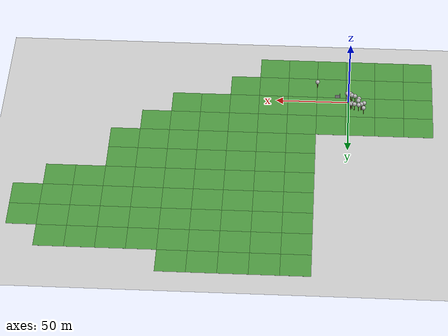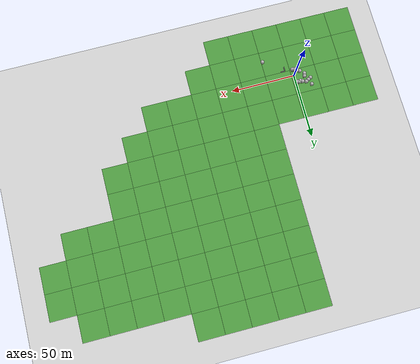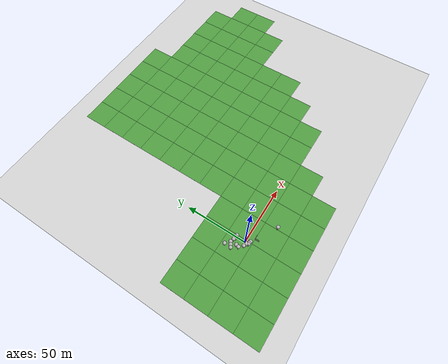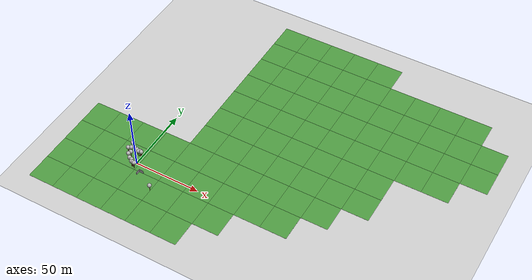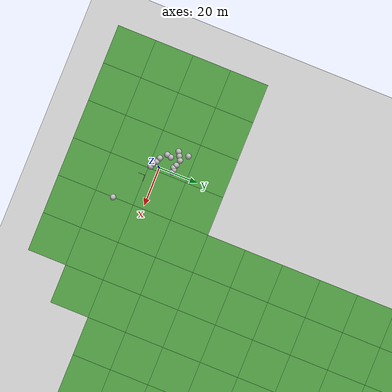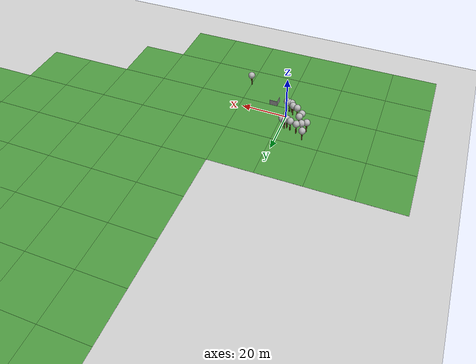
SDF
<sdf version="1.6">
 <world name="default">
  <model name="ground_plane">
   <static>1</static>
   <link name="link">
    <collision name="collision">
     <geometry><plane><normal>0 0 1</normal><size>100 100</size></plane></geometry>
     <surface><friction><ode><mu>100</mu><mu2>50</mu2></ode></friction></surface>
    </collision>
    <visual name="visual">
     <cast_shadows>0</cast_shadows>
     <geometry><plane><normal>0 0 1</normal><size>100 100</size></plane></geometry>
     <material>
      <script><uri>file://media/materials/scripts/gazebo.material</uri><name>Gazebo/Grey</name></script>
     </material>
    </visual>
   </link>
  </model>
  <model name="One_wall">
   <pose>7.58934 -6.85362 0 0 -0 0</pose>
   <link name="Wall_14">
    <collision name="Wall_14_Collision">
     <geometry><box><size>3.5 0.15 2.5</size></box></geometry>
     <pose>0 0 1.25 0 -0 0</pose>
    </collision>
    <visual name="Wall_14_Visual">
     <pose>0 0 1.25 0 -0 0</pose>
     <geometry><box><size>3.5 0.15 2.5</size></box></geometry>
     <material>
      <script><uri>file://media/materials/scripts/gazebo.material</uri><name>Gazebo/Grey</name></script>
      <ambient>1 1 1 1</ambient>
     </material>
    </visual>
    <pose>0 1.675 0 0 -0 0</pose>
   </link>
   <link name="Wall_4">
    <collision name="Wall_4_Collision">
     <geometry><box><size>3.5 0.15 2.5</size></box></geometry>
     <pose>0 0 1.25 0 -0 0</pose>
    </collision>
    <visual name="Wall_4_Visual">
     <pose>0 0 1.25 0 -0 0</pose>
     <geometry><box><size>3.5 0.15 2.5</size></box></geometry>
     <material>
      <script><uri>file://media/materials/scripts/gazebo.material</uri><name>Gazebo/Grey</name></script>
      <ambient>1 1 1 1</ambient>
     </material>
    </visual>
    <pose>-1.675 0 0 0 -0 1.5708</pose>
   </link>
   <static>1</static>
  </model>
  <light name="sun" type="directional">
   <pose>0 0 10 0 -0 0</pose>
   <diffuse>0.8 0.8 0.8 1</diffuse>
   <specular>0.1 0.1 0.1 1</specular>
   <attenuation>
    <range>1000</range>
    <constant>0.9</constant>
    <linear>0.01</linear>
    <quadratic>0.001</quadratic>
   </attenuation>
   <direction>-0.5 0.5 -1</direction>
  </light>
  <spherical_coordinates>
   <surface_model>EARTH_WGS84</surface_model>
   <latitude_deg>47.3667</latitude_deg>
   <longitude_deg>8.55</longitude_deg>
   <elevation>500</elevation>
   <heading_deg>0</heading_deg>
  </spherical_coordinates>
  <physics name="default_physics" default="0" type="ode">
   <ode>
    <solver>
     <type>quick</type>
     <iters>1000</iters>
     <sor>1.3</sor>
     <use_dynamic_moi_rescaling>0</use_dynamic_moi_rescaling>
    </solver>
    <constraints>
     <cfm>0</cfm>
     <erp>0.2</erp>
     <contact_max_correcting_vel>100</contact_max_correcting_vel>
     <contact_surface_layer>0.001</contact_surface_layer>
    </constraints>
   </ode>
   <max_step_size>0.01</max_step_size>
   <real_time_factor>1</real_time_factor>
   <real_time_update_rate>100</real_time_update_rate>
  </physics>
  <gravity>0 0 -9.8</gravity>
  <magnetic_field>6e-06 2.3e-05 -4.2e-05</magnetic_field>
  <atmosphere type="adiabatic"/>
  <scene><ambient>0.4 0.4 0.4 1</ambient><background>0.7 0.7 0.7 1</background><shadows>1</shadows></scene>
  <model name="mybot">
   <link name="chassis">
    <inertial>
     <pose>0 0 0.1 0 -0 0</pose>
     <mass>10</mass>
     <inertia><ixx>0.5</ixx><ixy>0</ixy><ixz>0</ixz><iyy>1</iyy><iyz>0</iyz><izz>0.1</izz></inertia>
    </inertial>
    <collision name="chassis_fixed_joint_lump__collision_collision">
     <geometry><box><size>0.4 0.2 0.1</size></box></geometry>
    </collision>
    <collision name="chassis_fixed_joint_lump__caster_collision_collision_1">
     <pose>-0.15 0 -0.05 0 -0 0</pose>
     <geometry><sphere><radius>0.05</radius></sphere></geometry>
    </collision>
    <visual name="chassis_visual_visual">
     <geometry><box><size>0.4 0.2 0.1</size></box></geometry>
     <material>
      <script><name>Gazebo/Orange</name><uri>file://media/materials/scripts/gazebo.material</uri></script>
     </material>
    </visual>
    <visual name="chassis_fixed_joint_lump__caster_visual_visual_1">
     <pose>-0.15 0 -0.05 0 -0 0</pose>
     <geometry><sphere><radius>0.05</radius></sphere></geometry>
    </visual>
   </link>
   <link name="left_wheel">
    <pose>0.1 0.15 0 0 -0 0</pose>
    <inertial>
     <pose>0 0 0 -0 1.5707 1.5707</pose>
     <mass>5</mass>
     <inertia><ixx>1</ixx><ixy>0</ixy><ixz>0</ixz><iyy>1</iyy><iyz>0</iyz><izz>1</izz></inertia>
    </inertial>
    <collision name="left_wheel_fixed_joint_lump__collision_collision">
     <pose>0 0 0 3.14159 1.57079 -1.57089</pose>
     <geometry><cylinder><length>0.05</length><radius>0.1</radius></cylinder></geometry>
    </collision>
    <visual name="left_wheel_visual_visual">
     <pose>0 0 0 3.14159 1.57079 -1.57089</pose>
     <geometry><cylinder><length>0.05</length><radius>0.1</radius></cylinder></geometry>
    </visual>
   </link>
   <joint name="left_wheel_hinge" type="revolute">
    <child>left_wheel</child>
    <parent>chassis</parent>
    <axis>
     <xyz>0 1 0</xyz>
     <limit><lower>-1e+16</lower><upper>1e+16</upper></limit>
     <dynamics><spring_reference>0</spring_reference><spring_stiffness>0</spring_stiffness></dynamics>
     <use_parent_model_frame>1</use_parent_model_frame>
    </axis>
   </joint>
   <link name="right_wheel">
    <pose>0.1 -0.15 0 0 -0 0</pose>
    <inertial>
     <pose>0 0 0 -0 1.5707 1.5707</pose>
     <mass>5</mass>
     <inertia><ixx>1</ixx><ixy>0</ixy><ixz>0</ixz><iyy>1</iyy><iyz>0</iyz><izz>1</izz></inertia>
    </inertial>
    <collision name="right_wheel_fixed_joint_lump__collision_collision">
     <pose>0 0 0 3.14159 1.57079 -1.57089</pose>
     <geometry><cylinder><length>0.05</length><radius>0.1</radius></cylinder></geometry>
    </collision>
    <visual name="right_wheel_visual_visual">
     <pose>0 0 0 3.14159 1.57079 -1.57089</pose>
     <geometry><cylinder><length>0.05</length><radius>0.1</radius></cylinder></geometry>
    </visual>
   </link>
   <joint name="right_wheel_hinge" type="revolute">
    <child>right_wheel</child>
    <parent>chassis</parent>
    <axis>
     <xyz>0 1 0</xyz>
     <limit><lower>-1e+16</lower><upper>1e+16</upper></limit>
     <dynamics><spring_reference>0</spring_reference><spring_stiffness>0</spring_stiffness></dynamics>
     <use_parent_model_frame>1</use_parent_model_frame>
    </axis>
   </joint>
   <static>0</static>
   <plugin name="differential_drive_controller" filename="libgazebo_ros_diff_drive.so">
    <legacyMode>false</legacyMode>
    <alwaysOn>true</alwaysOn>
    <updateRate>20</updateRate>
    <leftJoint>left_wheel_hinge</leftJoint>
    <rightJoint>right_wheel_hinge</rightJoint>
    <wheelSeparation>0.4</wheelSeparation>
    <wheelDiameter>0.1</wheelDiameter>
    <torque>20</torque>
    <commandTopic>cmd_vel</commandTopic>
    <odometryTopic>odom</odometryTopic>
    <odometryFrame>odom</odometryFrame>
    <robotBaseFrame>chassis</robotBaseFrame>
    <robotNamespace>/</robotNamespace>
   </plugin>
   <pose>0.586849 0.00472 0.1 -1e-06 -1e-06 0.026309</pose>
  </model>
  <model name="tree_simple">
   <static>1</static>
   <link name="link">
    <pose>0 0 0.1 0 -0 0</pose>
    <inertial>
     <mass>666</mass>
     <inertia>
      <ixx>0.0861167</ixx>
      <ixy>0</ixy>
      <ixz>0</ixz>
      <iyy>0.0861167</iyy>
      <iyz>0</iyz>
      <izz>0.0861167</izz>
     </inertia>
    </inertial>
    <collision name="collision_trunk">
     <pose>0 0 2 0 -0 0</pose>
     <geometry><cylinder><radius>0.25</radius><length>4</length></cylinder></geometry>
     <surface>
      <contact>
       <poissons_ratio>0.347</poissons_ratio>
       <elastic_modulus>8.8e+09</elastic_modulus>
       <ode><kp>100000</kp><kd>100</kd><max_vel>100</max_vel><min_depth>0.001</min_depth></ode>
      </contact>
      <friction>
       <torsional>
        <coefficient>1</coefficient>
        <use_patch_radius>0</use_patch_radius>
        <surface_radius>0.01</surface_radius>
       </torsional>
      </friction>
     </surface>
    </collision>
    <collision name="collision_treetop">
     <pose>0 0 5.2 0 -0 0</pose>
     <geometry><sphere><radius>1.5</radius></sphere></geometry>
     <surface>
      <contact>
       <poissons_ratio>0.347</poissons_ratio>
       <elastic_modulus>8.8e+09</elastic_modulus>
       <ode><kp>100000</kp><kd>100</kd><max_vel>100</max_vel><min_depth>0.001</min_depth></ode>
      </contact>
      <friction>
       <torsional>
        <coefficient>1</coefficient>
        <use_patch_radius>0</use_patch_radius>
        <surface_radius>0.01</surface_radius>
       </torsional>
      </friction>
     </surface>
    </collision>
    <visual name="trunk">
     <pose>0 0 2 0 -0 0</pose>
     <geometry><cylinder><radius>0.25</radius><length>4</length></cylinder></geometry>
     <material>
      <script>
       <uri>model://tree_simple/scripts</uri>
       <uri>model://tree_simple/materials/textures</uri>
       <name>TreeSimple/Trunk</name>
      </script>
     </material>
    </visual>
    <visual name="treetop">
     <pose>0 0 5.2 0 -0 0</pose>
     <geometry><sphere><radius>1.5</radius></sphere></geometry>
     <material>
      <script>
       <uri>model://tree_simple/scripts</uri>
       <uri>model://tree_simple/materials/textures</uri>
       <name>TreeSimple/Treetop</name>
      </script>
     </material>
    </visual>
   </link>
   <pose>-10.4753 11.3235 0 0 -0 0</pose>
  </model>
  <model name="grass_plane">
   <static>1</static>
   <link name="link">
    <collision name="collision">
     <geometry><plane><normal>0 0 1</normal><size>500 500</size></plane></geometry>
     <surface><friction><ode><mu>0.5</mu><mu2>0.5</mu2></ode></friction></surface>
    </collision>
    <visual name="visual_0">
     <pose>-40 -40 0 0 -0 0</pose>
     <cast_shadows>0</cast_shadows>
     <geometry><plane><normal>0 0 1</normal><size>20 20</size></plane></geometry>
     <material>
      <script>
       <uri>model://grass_plane/materials/scripts</uri>
       <uri>model://grass_plane/materials/textures</uri>
       <name>vrc/grass</name>
      </script>
     </material>
    </visual>
    <visual name="visual_1">
     <pose>-20 -40 0 0 -0 0</pose>
     <cast_shadows>0</cast_shadows>
     <geometry><plane><normal>0 0 1</normal><size>20 20</size></plane></geometry>
     <material>
      <script>
       <uri>model://grass_plane/materials/scripts</uri>
       <uri>model://grass_plane/materials/textures</uri>
       <name>vrc/grass</name>
      </script>
     </material>
    </visual>
    <visual name="visual_2">
     <pose>0 -40 0 0 -0 0</pose>
     <cast_shadows>0</cast_shadows>
     <geometry><plane><normal>0 0 1</normal><size>20 20</size></plane></geometry>
     <material>
      <script>
       <uri>model://grass_plane/materials/scripts</uri>
       <uri>model://grass_plane/materials/textures</uri>
       <name>vrc/grass</name>
      </script>
     </material>
    </visual>
    <visual name="visual_3">
     <pose>20 -40 0 0 -0 0</pose>
     <cast_shadows>0</cast_shadows>
     <geometry><plane><normal>0 0 1</normal><size>20 20</size></plane></geometry>
     <material>
      <script>
       <uri>model://grass_plane/materials/scripts</uri>
       <uri>model://grass_plane/materials/textures</uri>
       <name>vrc/grass</name>
      </script>
     </material>
    </visual>
    <visual name="visual_4">
     <pose>40 -40 0 0 -0 0</pose>
     <cast_shadows>0</cast_shadows>
     <geometry><plane><normal>0 0 1</normal><size>20 20</size></plane></geometry>
     <material>
      <script>
       <uri>model://grass_plane/materials/scripts</uri>
       <uri>model://grass_plane/materials/textures</uri>
       <name>vrc/grass</name>
      </script>
     </material>
    </visual>
    <visual name="visual_5">
     <pose>60 -40 0 0 -0 0</pose>
     <cast_shadows>0</cast_shadows>
     <geometry><plane><normal>0 0 1</normal><size>20 20</size></plane></geometry>
     <material>
      <script>
       <uri>model://grass_plane/materials/scripts</uri>
       <uri>model://grass_plane/materials/textures</uri>
       <name>vrc/grass</name>
      </script>
     </material>
    </visual>
    <visual name="visual_6">
     <pose>-40 -20 0 0 -0 0</pose>
     <cast_shadows>0</cast_shadows>
     <geometry><plane><normal>0 0 1</normal><size>20 20</size></plane></geometry>
     <material>
      <script>
       <uri>model://grass_plane/materials/scripts</uri>
       <uri>model://grass_plane/materials/textures</uri>
       <name>vrc/grass</name>
      </script>
     </material>
    </visual>
    <visual name="visual_7">
     <pose>-20 -20 0 0 -0 0</pose>
     <cast_shadows>0</cast_shadows>
     <geometry><plane><normal>0 0 1</normal><size>20 20</size></plane></geometry>
     <material>
      <script>
       <uri>model://grass_plane/materials/scripts</uri>
       <uri>model://grass_plane/materials/textures</uri>
       <name>vrc/grass</name>
      </script>
     </material>
    </visual>
    <visual name="visual_8">
     <pose>0 -20 0 0 -0 0</pose>
     <cast_shadows>0</cast_shadows>
     <geometry><plane><normal>0 0 1</normal><size>20 20</size></plane></geometry>
     <material>
      <script>
       <uri>model://grass_plane/materials/scripts</uri>
       <uri>model://grass_plane/materials/textures</uri>
       <name>vrc/grass</name>
      </script>
     </material>
    </visual>
    <visual name="visual_9">
     <pose>20 -20 0 0 -0 0</pose>
     <cast_shadows>0</cast_shadows>
     <geometry><plane><normal>0 0 1</normal><size>20 20</size></plane></geometry>
     <material>
      <script>
       <uri>model://grass_plane/materials/scripts</uri>
       <uri>model://grass_plane/materials/textures</uri>
       <name>vrc/grass</name>
      </script>
     </material>
    </visual>
    <visual name="visual_10">
     <pose>40 -20 0 0 -0 0</pose>
     <cast_shadows>0</cast_shadows>
     <geometry><plane><normal>0 0 1</normal><size>20 20</size></plane></geometry>
     <material>
      <script>
       <uri>model://grass_plane/materials/scripts</uri>
       <uri>model://grass_plane/materials/textures</uri>
       <name>vrc/grass</name>
      </script>
     </material>
    </visual>
    <visual name="visual_11">
     <pose>60 -20 0 0 -0 0</pose>
     <cast_shadows>0</cast_shadows>
     <geometry><plane><normal>0 0 1</normal><size>20 20</size></plane></geometry>
     <material>
      <script>
       <uri>model://grass_plane/materials/scripts</uri>
       <uri>model://grass_plane/materials/textures</uri>
       <name>vrc/grass</name>
      </script>
     </material>
    </visual>
    <visual name="visual_12">
     <pose>80 -20 0 0 -0 0</pose>
     <cast_shadows>0</cast_shadows>
     <geometry><plane><normal>0 0 1</normal><size>20 20</size></plane></geometry>
     <material>
      <script>
       <uri>model://grass_plane/materials/scripts</uri>
       <uri>model://grass_plane/materials/textures</uri>
       <name>vrc/grass</name>
      </script>
     </material>
    </visual>
    <visual name="visual_13">
     <pose>-40 0 0 0 -0 0</pose>
     <cast_shadows>0</cast_shadows>
     <geometry><plane><normal>0 0 1</normal><size>20 20</size></plane></geometry>
     <material>
      <script>
       <uri>model://grass_plane/materials/scripts</uri>
       <uri>model://grass_plane/materials/textures</uri>
       <name>vrc/grass</name>
      </script>
     </material>
    </visual>
    <visual name="visual_14">
     <pose>-20 0 0 0 -0 0</pose>
     <cast_shadows>0</cast_shadows>
     <geometry><plane><normal>0 0 1</normal><size>20 20</size></plane></geometry>
     <material>
      <script>
       <uri>model://grass_plane/materials/scripts</uri>
       <uri>model://grass_plane/materials/textures</uri>
       <name>vrc/grass</name>
      </script>
     </material>
    </visual>
    <visual name="visual_15">
     <cast_shadows>0</cast_shadows>
     <geometry><plane><normal>0 0 1</normal><size>20 20</size></plane></geometry>
     <material>
      <script>
       <uri>model://grass_plane/materials/scripts</uri>
       <uri>model://grass_plane/materials/textures</uri>
       <name>vrc/grass</name>
      </script>
     </material>
    </visual>
    <visual name="visual_16">
     <pose>20 0 0 0 -0 0</pose>
     <cast_shadows>0</cast_shadows>
     <geometry><plane><normal>0 0 1</normal><size>20 20</size></plane></geometry>
     <material>
      <script>
       <uri>model://grass_plane/materials/scripts</uri>
       <uri>model://grass_plane/materials/textures</uri>
       <name>vrc/grass</name>
      </script>
     </material>
    </visual>
    <visual name="visual_17">
     <pose>40 0 0 0 -0 0</pose>
     <cast_shadows>0</cast_shadows>
     <geometry><plane><normal>0 0 1</normal><size>20 20</size></plane></geometry>
     <material>
      <script>
       <uri>model://grass_plane/materials/scripts</uri>
       <uri>model://grass_plane/materials/textures</uri>
       <name>vrc/grass</name>
      </script>
     </material>
    </visual>
    <visual name="visual_18">
     <pose>60 0 0 0 -0 0</pose>
     <cast_shadows>0</cast_shadows>
     <geometry><plane><normal>0 0 1</normal><size>20 20</size></plane></geometry>
     <material>
      <script>
       <uri>model://grass_plane/materials/scripts</uri>
       <uri>model://grass_plane/materials/textures</uri>
       <name>vrc/grass</name>
      </script>
     </material>
    </visual>
    <visual name="visual_19">
     <pose>80 0 0 0 -0 0</pose>
     <cast_shadows>0</cast_shadows>
     <geometry><plane><normal>0 0 1</normal><size>20 20</size></plane></geometry>
     <material>
      <script>
       <uri>model://grass_plane/materials/scripts</uri>
       <uri>model://grass_plane/materials/textures</uri>
       <name>vrc/grass</name>
      </script>
     </material>
    </visual>
    <visual name="visual_20">
     <pose>100 0 0 0 -0 0</pose>
     <cast_shadows>0</cast_shadows>
     <geometry><plane><normal>0 0 1</normal><size>20 20</size></plane></geometry>
     <material>
      <script>
       <uri>model://grass_plane/materials/scripts</uri>
       <uri>model://grass_plane/materials/textures</uri>
       <name>vrc/grass</name>
      </script>
     </material>
    </visual>
    <visual name="visual_21">
     <pose>120 0 0 0 -0 0</pose>
     <cast_shadows>0</cast_shadows>
     <geometry><plane><normal>0 0 1</normal><size>20 20</size></plane></geometry>
     <material>
      <script>
       <uri>model://grass_plane/materials/scripts</uri>
       <uri>model://grass_plane/materials/textures</uri>
       <name>vrc/grass</name>
      </script>
     </material>
    </visual>
    <visual name="visual_22">
     <pose>-40 20 0 0 -0 0</pose>
     <cast_shadows>0</cast_shadows>
     <geometry><plane><normal>0 0 1</normal><size>20 20</size></plane></geometry>
     <material>
      <script>
       <uri>model://grass_plane/materials/scripts</uri>
       <uri>model://grass_plane/materials/textures</uri>
       <name>vrc/grass</name>
      </script>
     </material>
    </visual>
    <visual name="visual_23">
     <pose>-20 20 0 0 -0 0</pose>
     <cast_shadows>0</cast_shadows>
     <geometry><plane><normal>0 0 1</normal><size>20 20</size></plane></geometry>
     <material>
      <script>
       <uri>model://grass_plane/materials/scripts</uri>
       <uri>model://grass_plane/materials/textures</uri>
       <name>vrc/grass</name>
      </script>
     </material>
    </visual>
    <visual name="visual_24">
     <pose>0 20 0 0 -0 0</pose>
     <cast_shadows>0</cast_shadows>
     <geometry><plane><normal>0 0 1</normal><size>20 20</size></plane></geometry>
     <material>
      <script>
       <uri>model://grass_plane/materials/scripts</uri>
       <uri>model://grass_plane/materials/textures</uri>
       <name>vrc/grass</name>
      </script>
     </material>
    </visual>
    <visual name="visual_25">
     <pose>20 20 0 0 -0 0</pose>
     <cast_shadows>0</cast_shadows>
     <geometry><plane><normal>0 0 1</normal><size>20 20</size></plane></geometry>
     <material>
      <script>
       <uri>model://grass_plane/materials/scripts</uri>
       <uri>model://grass_plane/materials/textures</uri>
       <name>vrc/grass</name>
      </script>
     </material>
    </visual>
    <visual name="visual_26">
     <pose>40 20 0 0 -0 0</pose>
     <cast_shadows>0</cast_shadows>
     <geometry><plane><normal>0 0 1</normal><size>20 20</size></plane></geometry>
     <material>
      <script>
       <uri>model://grass_plane/materials/scripts</uri>
       <uri>model://grass_plane/materials/textures</uri>
       <name>vrc/grass</name>
      </script>
     </material>
    </visual>
    <visual name="visual_27">
     <pose>60 20 0 0 -0 0</pose>
     <cast_shadows>0</cast_shadows>
     <geometry><plane><normal>0 0 1</normal><size>20 20</size></plane></geometry>
     <material>
      <script>
       <uri>model://grass_plane/materials/scripts</uri>
       <uri>model://grass_plane/materials/textures</uri>
       <name>vrc/grass</name>
      </script>
     </material>
    </visual>
    <visual name="visual_28">
     <pose>80 20 0 0 -0 0</pose>
     <cast_shadows>0</cast_shadows>
     <geometry><plane><normal>0 0 1</normal><size>20 20</size></plane></geometry>
     <material>
      <script>
       <uri>model://grass_plane/materials/scripts</uri>
       <uri>model://grass_plane/materials/textures</uri>
       <name>vrc/grass</name>
      </script>
     </material>
    </visual>
    <visual name="visual_29">
     <pose>100 20 0 0 -0 0</pose>
     <cast_shadows>0</cast_shadows>
     <geometry><plane><normal>0 0 1</normal><size>20 20</size></plane></geometry>
     <material>
      <script>
       <uri>model://grass_plane/materials/scripts</uri>
       <uri>model://grass_plane/materials/textures</uri>
       <name>vrc/grass</name>
      </script>
     </material>
    </visual>
    <visual name="visual_30">
     <pose>120 20 0 0 -0 0</pose>
     <cast_shadows>0</cast_shadows>
     <geometry><plane><normal>0 0 1</normal><size>20 20</size></plane></geometry>
     <material>
      <script>
       <uri>model://grass_plane/materials/scripts</uri>
       <uri>model://grass_plane/materials/textures</uri>
       <name>vrc/grass</name>
      </script>
     </material>
    </visual>
    <visual name="visual_31">
     <pose>140 20 0 0 -0 0</pose>
     <cast_shadows>0</cast_shadows>
     <geometry><plane><normal>0 0 1</normal><size>20 20</size></plane></geometry>
     <material>
      <script>
       <uri>model://grass_plane/materials/scripts</uri>
       <uri>model://grass_plane/materials/textures</uri>
       <name>vrc/grass</name>
      </script>
     </material>
    </visual>
    <visual name="visual_32">
     <pose>40 40 0 0 -0 0</pose>
     <cast_shadows>0</cast_shadows>
     <geometry><plane><normal>0 0 1</normal><size>20 20</size></plane></geometry>
     <material>
      <script>
       <uri>model://grass_plane/materials/scripts</uri>
       <uri>model://grass_plane/materials/textures</uri>
       <name>vrc/grass</name>
      </script>
     </material>
    </visual>
    <visual name="visual_33">
     <pose>60 40 0 0 -0 0</pose>
     <cast_shadows>0</cast_shadows>
     <geometry><plane><normal>0 0 1</normal><size>20 20</size></plane></geometry>
     <material>
      <script>
       <uri>model://grass_plane/materials/scripts</uri>
       <uri>model://grass_plane/materials/textures</uri>
       <name>vrc/grass</name>
      </script>
     </material>
    </visual>
    <visual name="visual_34">
     <pose>80 40 0 0 -0 0</pose>
     <cast_shadows>0</cast_shadows>
     <geometry><plane><normal>0 0 1</normal><size>20 20</size></plane></geometry>
     <material>
      <script>
       <uri>model://grass_plane/materials/scripts</uri>
       <uri>model://grass_plane/materials/textures</uri>
       <name>vrc/grass</name>
      </script>
     </material>
    </visual>
    <visual name="visual_35">
     <pose>100 40 0 0 -0 0</pose>
     <cast_shadows>0</cast_shadows>
     <geometry><plane><normal>0 0 1</normal><size>20 20</size></plane></geometry>
     <material>
      <script>
       <uri>model://grass_plane/materials/scripts</uri>
       <uri>model://grass_plane/materials/textures</uri>
       <name>vrc/grass</name>
      </script>
     </material>
    </visual>
    <visual name="visual_36">
     <pose>120 40 0 0 -0 0</pose>
     <cast_shadows>0</cast_shadows>
     <geometry><plane><normal>0 0 1</normal><size>20 20</size></plane></geometry>
     <material>
      <script>
       <uri>model://grass_plane/materials/scripts</uri>
       <uri>model://grass_plane/materials/textures</uri>
       <name>vrc/grass</name>
      </script>
     </material>
    </visual>
    <visual name="visual_37">
     <pose>140 40 0 0 -0 0</pose>
     <cast_shadows>0</cast_shadows>
     <geometry><plane><normal>0 0 1</normal><size>20 20</size></plane></geometry>
     <material>
      <script>
       <uri>model://grass_plane/materials/scripts</uri>
       <uri>model://grass_plane/materials/textures</uri>
       <name>vrc/grass</name>
      </script>
     </material>
    </visual>
    <visual name="visual_38">
     <pose>160 40 0 0 -0 0</pose>
     <cast_shadows>0</cast_shadows>
     <geometry><plane><normal>0 0 1</normal><size>20 20</size></plane></geometry>
     <material>
      <script>
       <uri>model://grass_plane/materials/scripts</uri>
       <uri>model://grass_plane/materials/textures</uri>
       <name>vrc/grass</name>
      </script>
     </material>
    </visual>
    <visual name="visual_39">
     <pose>40 60 0 0 -0 0</pose>
     <cast_shadows>0</cast_shadows>
     <geometry><plane><normal>0 0 1</normal><size>20 20</size></plane></geometry>
     <material>
      <script>
       <uri>model://grass_plane/materials/scripts</uri>
       <uri>model://grass_plane/materials/textures</uri>
       <name>vrc/grass</name>
      </script>
     </material>
    </visual>
    <visual name="visual_40">
     <pose>60 60 0 0 -0 0</pose>
     <cast_shadows>0</cast_shadows>
     <geometry><plane><normal>0 0 1</normal><size>20 20</size></plane></geometry>
     <material>
      <script>
       <uri>model://grass_plane/materials/scripts</uri>
       <uri>model://grass_plane/materials/textures</uri>
       <name>vrc/grass</name>
      </script>
     </material>
    </visual>
    <visual name="visual_41">
     <pose>80 60 0 0 -0 0</pose>
     <cast_shadows>0</cast_shadows>
     <geometry><plane><normal>0 0 1</normal><size>20 20</size></plane></geometry>
     <material>
      <script>
       <uri>model://grass_plane/materials/scripts</uri>
       <uri>model://grass_plane/materials/textures</uri>
       <name>vrc/grass</name>
      </script>
     </material>
    </visual>
    <visual name="visual_42">
     <pose>100 60 0 0 -0 0</pose>
     <cast_shadows>0</cast_shadows>
     <geometry><plane><normal>0 0 1</normal><size>20 20</size></plane></geometry>
     <material>
      <script>
       <uri>model://grass_plane/materials/scripts</uri>
       <uri>model://grass_plane/materials/textures</uri>
       <name>vrc/grass</name>
      </script>
     </material>
    </visual>
    <visual name="visual_43">
     <pose>120 60 0 0 -0 0</pose>
     <cast_shadows>0</cast_shadows>
     <geometry><plane><normal>0 0 1</normal><size>20 20</size></plane></geometry>
     <material>
      <script>
       <uri>model://grass_plane/materials/scripts</uri>
       <uri>model://grass_plane/materials/textures</uri>
       <name>vrc/grass</name>
      </script>
     </material>
    </visual>
    <visual name="visual_44">
     <pose>140 60 0 0 -0 0</pose>
     <cast_shadows>0</cast_shadows>
     <geometry><plane><normal>0 0 1</normal><size>20 20</size></plane></geometry>
     <material>
      <script>
       <uri>model://grass_plane/materials/scripts</uri>
       <uri>model://grass_plane/materials/textures</uri>
       <name>vrc/grass</name>
      </script>
     </material>
    </visual>
    <visual name="visual_45">
     <pose>160 60 0 0 -0 0</pose>
     <cast_shadows>0</cast_shadows>
     <geometry><plane><normal>0 0 1</normal><size>20 20</size></plane></geometry>
     <material>
      <script>
       <uri>model://grass_plane/materials/scripts</uri>
       <uri>model://grass_plane/materials/textures</uri>
       <name>vrc/grass</name>
      </script>
     </material>
    </visual>
    <visual name="visual_46">
     <pose>40 80 0 0 -0 0</pose>
     <cast_shadows>0</cast_shadows>
     <geometry><plane><normal>0 0 1</normal><size>20 20</size></plane></geometry>
     <material>
      <script>
       <uri>model://grass_plane/materials/scripts</uri>
       <uri>model://grass_plane/materials/textures</uri>
       <name>vrc/grass</name>
      </script>
     </material>
    </visual>
    <visual name="visual_47">
     <pose>60 80 0 0 -0 0</pose>
     <cast_shadows>0</cast_shadows>
     <geometry><plane><normal>0 0 1</normal><size>20 20</size></plane></geometry>
     <material>
      <script>
       <uri>model://grass_plane/materials/scripts</uri>
       <uri>model://grass_plane/materials/textures</uri>
       <name>vrc/grass</name>
      </script>
     </material>
    </visual>
    <visual name="visual_48">
     <pose>80 80 0 0 -0 0</pose>
     <cast_shadows>0</cast_shadows>
     <geometry><plane><normal>0 0 1</normal><size>20 20</size></plane></geometry>
     <material>
      <script>
       <uri>model://grass_plane/materials/scripts</uri>
       <uri>model://grass_plane/materials/textures</uri>
       <name>vrc/grass</name>
      </script>
     </material>
    </visual>
    <visual name="visual_49">
     <pose>100 80 0 0 -0 0</pose>
     <cast_shadows>0</cast_shadows>
     <geometry><plane><normal>0 0 1</normal><size>20 20</size></plane></geometry>
     <material>
      <script>
       <uri>model://grass_plane/materials/scripts</uri>
       <uri>model://grass_plane/materials/textures</uri>
       <name>vrc/grass</name>
      </script>
     </material>
    </visual>
    <visual name="visual_50">
     <pose>120 80 0 0 -0 0</pose>
     <cast_shadows>0</cast_shadows>
     <geometry><plane><normal>0 0 1</normal><size>20 20</size></plane></geometry>
     <material>
      <script>
       <uri>model://grass_plane/materials/scripts</uri>
       <uri>model://grass_plane/materials/textures</uri>
       <name>vrc/grass</name>
      </script>
     </material>
    </visual>
    <visual name="visual_51">
     <pose>140 80 0 0 -0 0</pose>
     <cast_shadows>0</cast_shadows>
     <geometry><plane><normal>0 0 1</normal><size>20 20</size></plane></geometry>
     <material>
      <script>
       <uri>model://grass_plane/materials/scripts</uri>
       <uri>model://grass_plane/materials/textures</uri>
       <name>vrc/grass</name>
      </script>
     </material>
    </visual>
    <visual name="visual_52">
     <pose>160 80 0 0 -0 0</pose>
     <cast_shadows>0</cast_shadows>
     <geometry><plane><normal>0 0 1</normal><size>20 20</size></plane></geometry>
     <material>
      <script>
       <uri>model://grass_plane/materials/scripts</uri>
       <uri>model://grass_plane/materials/textures</uri>
       <name>vrc/grass</name>
      </script>
     </material>
    </visual>
    <visual name="visual_53">
     <pose>180 80 0 0 -0 0</pose>
     <cast_shadows>0</cast_shadows>
     <geometry><plane><normal>0 0 1</normal><size>20 20</size></plane></geometry>
     <material>
      <script>
       <uri>model://grass_plane/materials/scripts</uri>
       <uri>model://grass_plane/materials/textures</uri>
       <name>vrc/grass</name>
      </script>
     </material>
    </visual>
    <visual name="visual_54">
     <pose>200 80 0 0 -0 0</pose>
     <cast_shadows>0</cast_shadows>
     <geometry><plane><normal>0 0 1</normal><size>20 20</size></plane></geometry>
     <material>
      <script>
       <uri>model://grass_plane/materials/scripts</uri>
       <uri>model://grass_plane/materials/textures</uri>
       <name>vrc/grass</name>
      </script>
     </material>
    </visual>
    <visual name="visual_55">
     <pose>40 100 0 0 -0 0</pose>
     <cast_shadows>0</cast_shadows>
     <geometry><plane><normal>0 0 1</normal><size>20 20</size></plane></geometry>
     <material>
      <script>
       <uri>model://grass_plane/materials/scripts</uri>
       <uri>model://grass_plane/materials/textures</uri>
       <name>vrc/grass</name>
      </script>
     </material>
    </visual>
    <visual name="visual_56">
     <pose>60 100 0 0 -0 0</pose>
     <cast_shadows>0</cast_shadows>
     <geometry><plane><normal>0 0 1</normal><size>20 20</size></plane></geometry>
     <material>
      <script>
       <uri>model://grass_plane/materials/scripts</uri>
       <uri>model://grass_plane/materials/textures</uri>
       <name>vrc/grass</name>
      </script>
     </material>
    </visual>
    <visual name="visual_57">
     <pose>80 100 0 0 -0 0</pose>
     <cast_shadows>0</cast_shadows>
     <geometry><plane><normal>0 0 1</normal><size>20 20</size></plane></geometry>
     <material>
      <script>
       <uri>model://grass_plane/materials/scripts</uri>
       <uri>model://grass_plane/materials/textures</uri>
       <name>vrc/grass</name>
      </script>
     </material>
    </visual>
    <visual name="visual_58">
     <pose>100 100 0 0 -0 0</pose>
     <cast_shadows>0</cast_shadows>
     <geometry><plane><normal>0 0 1</normal><size>20 20</size></plane></geometry>
     <material>
      <script>
       <uri>model://grass_plane/materials/scripts</uri>
       <uri>model://grass_plane/materials/textures</uri>
       <name>vrc/grass</name>
      </script>
     </material>
    </visual>
    <visual name="visual_59">
     <pose>120 100 0 0 -0 0</pose>
     <cast_shadows>0</cast_shadows>
     <geometry><plane><normal>0 0 1</normal><size>20 20</size></plane></geometry>
     <material>
      <script>
       <uri>model://grass_plane/materials/scripts</uri>
       <uri>model://grass_plane/materials/textures</uri>
       <name>vrc/grass</name>
      </script>
     </material>
    </visual>
    <visual name="visual_60">
     <pose>140 100 0 0 -0 0</pose>
     <cast_shadows>0</cast_shadows>
     <geometry><plane><normal>0 0 1</normal><size>20 20</size></plane></geometry>
     <material>
      <script>
       <uri>model://grass_plane/materials/scripts</uri>
       <uri>model://grass_plane/materials/textures</uri>
       <name>vrc/grass</name>
      </script>
     </material>
    </visual>
    <visual name="visual_61">
     <pose>160 100 0 0 -0 0</pose>
     <cast_shadows>0</cast_shadows>
     <geometry><plane><normal>0 0 1</normal><size>20 20</size></plane></geometry>
     <material>
      <script>
       <uri>model://grass_plane/materials/scripts</uri>
       <uri>model://grass_plane/materials/textures</uri>
       <name>vrc/grass</name>
      </script>
     </material>
    </visual>
    <visual name="visual_62">
     <pose>180 100 0 0 -0 0</pose>
     <cast_shadows>0</cast_shadows>
     <geometry><plane><normal>0 0 1</normal><size>20 20</size></plane></geometry>
     <material>
      <script>
       <uri>model://grass_plane/materials/scripts</uri>
       <uri>model://grass_plane/materials/textures</uri>
       <name>vrc/grass</name>
      </script>
     </material>
    </visual>
    <visual name="visual_63">
     <pose>200 100 0 0 -0 0</pose>
     <cast_shadows>0</cast_shadows>
     <geometry><plane><normal>0 0 1</normal><size>20 20</size></plane></geometry>
     <material>
      <script>
       <uri>model://grass_plane/materials/scripts</uri>
       <uri>model://grass_plane/materials/textures</uri>
       <name>vrc/grass</name>
      </script>
     </material>
    </visual>
    <visual name="visual_63a">
     <pose>220 100 0 0 -0 0</pose>
     <cast_shadows>0</cast_shadows>
     <geometry><plane><normal>0 0 1</normal><size>20 20</size></plane></geometry>
     <material>
      <script>
       <uri>model://grass_plane/materials/scripts</uri>
       <uri>model://grass_plane/materials/textures</uri>
       <name>vrc/grass</name>
      </script>
     </material>
    </visual>
    <visual name="visual_64">
     <pose>40 120 0 0 -0 0</pose>
     <cast_shadows>0</cast_shadows>
     <geometry><plane><normal>0 0 1</normal><size>20 20</size></plane></geometry>
     <material>
      <script>
       <uri>model://grass_plane/materials/scripts</uri>
       <uri>model://grass_plane/materials/textures</uri>
       <name>vrc/grass</name>
      </script>
     </material>
    </visual>
    <visual name="visual_65">
     <pose>60 120 0 0 -0 0</pose>
     <cast_shadows>0</cast_shadows>
     <geometry><plane><normal>0 0 1</normal><size>20 20</size></plane></geometry>
     <material>
      <script>
       <uri>model://grass_plane/materials/scripts</uri>
       <uri>model://grass_plane/materials/textures</uri>
       <name>vrc/grass</name>
      </script>
     </material>
    </visual>
    <visual name="visual_66">
     <pose>80 120 0 0 -0 0</pose>
     <cast_shadows>0</cast_shadows>
     <geometry><plane><normal>0 0 1</normal><size>20 20</size></plane></geometry>
     <material>
      <script>
       <uri>model://grass_plane/materials/scripts</uri>
       <uri>model://grass_plane/materials/textures</uri>
       <name>vrc/grass</name>
      </script>
     </material>
    </visual>
    <visual name="visual_67">
     <pose>100 120 0 0 -0 0</pose>
     <cast_shadows>0</cast_shadows>
     <geometry><plane><normal>0 0 1</normal><size>20 20</size></plane></geometry>
     <material>
      <script>
       <uri>model://grass_plane/materials/scripts</uri>
       <uri>model://grass_plane/materials/textures</uri>
       <name>vrc/grass</name>
      </script>
     </material>
    </visual>
    <visual name="visual_68">
     <pose>120 120 0 0 -0 0</pose>
     <cast_shadows>0</cast_shadows>
     <geometry><plane><normal>0 0 1</normal><size>20 20</size></plane></geometry>
     <material>
      <script>
       <uri>model://grass_plane/materials/scripts</uri>
       <uri>model://grass_plane/materials/textures</uri>
       <name>vrc/grass</name>
      </script>
     </material>
    </visual>
    <visual name="visual_69">
     <pose>140 120 0 0 -0 0</pose>
     <cast_shadows>0</cast_shadows>
     <geometry><plane><normal>0 0 1</normal><size>20 20</size></plane></geometry>
     <material>
      <script>
       <uri>model://grass_plane/materials/scripts</uri>
       <uri>model://grass_plane/materials/textures</uri>
       <name>vrc/grass</name>
      </script>
     </material>
    </visual>
    <visual name="visual_70">
     <pose>160 120 0 0 -0 0</pose>
     <cast_shadows>0</cast_shadows>
     <geometry><plane><normal>0 0 1</normal><size>20 20</size></plane></geometry>
     <material>
      <script>
       <uri>model://grass_plane/materials/scripts</uri>
       <uri>model://grass_plane/materials/textures</uri>
       <name>vrc/grass</name>
      </script>
     </material>
    </visual>
    <visual name="visual_71">
     <pose>180 120 0 0 -0 0</pose>
     <cast_shadows>0</cast_shadows>
     <geometry><plane><normal>0 0 1</normal><size>20 20</size></plane></geometry>
     <material>
      <script>
       <uri>model://grass_plane/materials/scripts</uri>
       <uri>model://grass_plane/materials/textures</uri>
       <name>vrc/grass</name>
      </script>
     </material>
    </visual>
    <visual name="visual_72">
     <pose>200 120 0 0 -0 0</pose>
     <cast_shadows>0</cast_shadows>
     <geometry><plane><normal>0 0 1</normal><size>20 20</size></plane></geometry>
     <material>
      <script>
       <uri>model://grass_plane/materials/scripts</uri>
       <uri>model://grass_plane/materials/textures</uri>
       <name>vrc/grass</name>
      </script>
     </material>
    </visual>
    <visual name="visual_72a">
     <pose>220 120 0 0 -0 0</pose>
     <cast_shadows>0</cast_shadows>
     <geometry><plane><normal>0 0 1</normal><size>20 20</size></plane></geometry>
     <material>
      <script>
       <uri>model://grass_plane/materials/scripts</uri>
       <uri>model://grass_plane/materials/textures</uri>
       <name>vrc/grass</name>
      </script>
     </material>
    </visual>
    <visual name="visual_73">
     <pose>40 140 0 0 -0 0</pose>
     <cast_shadows>0</cast_shadows>
     <geometry><plane><normal>0 0 1</normal><size>20 20</size></plane></geometry>
     <material>
      <script>
       <uri>model://grass_plane/materials/scripts</uri>
       <uri>model://grass_plane/materials/textures</uri>
       <name>vrc/grass</name>
      </script>
     </material>
    </visual>
    <visual name="visual_74">
     <pose>60 140 0 0 -0 0</pose>
     <cast_shadows>0</cast_shadows>
     <geometry><plane><normal>0 0 1</normal><size>20 20</size></plane></geometry>
     <material>
      <script>
       <uri>model://grass_plane/materials/scripts</uri>
       <uri>model://grass_plane/materials/textures</uri>
       <name>vrc/grass</name>
      </script>
     </material>
    </visual>
    <visual name="visual_75">
     <pose>80 140 0 0 -0 0</pose>
     <cast_shadows>0</cast_shadows>
     <geometry><plane><normal>0 0 1</normal><size>20 20</size></plane></geometry>
     <material>
      <script>
       <uri>model://grass_plane/materials/scripts</uri>
       <uri>model://grass_plane/materials/textures</uri>
       <name>vrc/grass</name>
      </script>
     </material>
    </visual>
    <visual name="visual_76">
     <pose>100 140 0 0 -0 0</pose>
     <cast_shadows>0</cast_shadows>
     <geometry><plane><normal>0 0 1</normal><size>20 20</size></plane></geometry>
     <material>
      <script>
       <uri>model://grass_plane/materials/scripts</uri>
       <uri>model://grass_plane/materials/textures</uri>
       <name>vrc/grass</name>
      </script>
     </material>
    </visual>
    <visual name="visual_77">
     <pose>120 140 0 0 -0 0</pose>
     <cast_shadows>0</cast_shadows>
     <geometry><plane><normal>0 0 1</normal><size>20 20</size></plane></geometry>
     <material>
      <script>
       <uri>model://grass_plane/materials/scripts</uri>
       <uri>model://grass_plane/materials/textures</uri>
       <name>vrc/grass</name>
      </script>
     </material>
    </visual>
    <visual name="visual_78">
     <pose>140 140 0 0 -0 0</pose>
     <cast_shadows>0</cast_shadows>
     <geometry><plane><normal>0 0 1</normal><size>20 20</size></plane></geometry>
     <material>
      <script>
       <uri>model://grass_plane/materials/scripts</uri>
       <uri>model://grass_plane/materials/textures</uri>
       <name>vrc/grass</name>
      </script>
     </material>
    </visual>
    <visual name="visual_79">
     <pose>160 140 0 0 -0 0</pose>
     <cast_shadows>0</cast_shadows>
     <geometry><plane><normal>0 0 1</normal><size>20 20</size></plane></geometry>
     <material>
      <script>
       <uri>model://grass_plane/materials/scripts</uri>
       <uri>model://grass_plane/materials/textures</uri>
       <name>vrc/grass</name>
      </script>
     </material>
    </visual>
    <visual name="visual_80">
     <pose>180 140 0 0 -0 0</pose>
     <cast_shadows>0</cast_shadows>
     <geometry><plane><normal>0 0 1</normal><size>20 20</size></plane></geometry>
     <material>
      <script>
       <uri>model://grass_plane/materials/scripts</uri>
       <uri>model://grass_plane/materials/textures</uri>
       <name>vrc/grass</name>
      </script>
     </material>
    </visual>
    <visual name="visual_81">
     <pose>200 140 0 0 -0 0</pose>
     <cast_shadows>0</cast_shadows>
     <geometry><plane><normal>0 0 1</normal><size>20 20</size></plane></geometry>
     <material>
      <script>
       <uri>model://grass_plane/materials/scripts</uri>
       <uri>model://grass_plane/materials/textures</uri>
       <name>vrc/grass</name>
      </script>
     </material>
    </visual>
    <visual name="visual_82">
     <pose>40 160 0 0 -0 0</pose>
     <cast_shadows>0</cast_shadows>
     <geometry><plane><normal>0 0 1</normal><size>20 20</size></plane></geometry>
     <material>
      <script>
       <uri>model://grass_plane/materials/scripts</uri>
       <uri>model://grass_plane/materials/textures</uri>
       <name>vrc/grass</name>
      </script>
     </material>
    </visual>
    <visual name="visual_83">
     <pose>60 160 0 0 -0 0</pose>
     <cast_shadows>0</cast_shadows>
     <geometry><plane><normal>0 0 1</normal><size>20 20</size></plane></geometry>
     <material>
      <script>
       <uri>model://grass_plane/materials/scripts</uri>
       <uri>model://grass_plane/materials/textures</uri>
       <name>vrc/grass</name>
      </script>
     </material>
    </visual>
    <visual name="visual_84">
     <pose>80 160 0 0 -0 0</pose>
     <cast_shadows>0</cast_shadows>
     <geometry><plane><normal>0 0 1</normal><size>20 20</size></plane></geometry>
     <material>
      <script>
       <uri>model://grass_plane/materials/scripts</uri>
       <uri>model://grass_plane/materials/textures</uri>
       <name>vrc/grass</name>
      </script>
     </material>
    </visual>
    <visual name="visual_85">
     <pose>100 160 0 0 -0 0</pose>
     <cast_shadows>0</cast_shadows>
     <geometry><plane><normal>0 0 1</normal><size>20 20</size></plane></geometry>
     <material>
      <script>
       <uri>model://grass_plane/materials/scripts</uri>
       <uri>model://grass_plane/materials/textures</uri>
       <name>vrc/grass</name>
      </script>
     </material>
    </visual>
    <visual name="visual_86">
     <pose>120 160 0 0 -0 0</pose>
     <cast_shadows>0</cast_shadows>
     <geometry><plane><normal>0 0 1</normal><size>20 20</size></plane></geometry>
     <material>
      <script>
       <uri>model://grass_plane/materials/scripts</uri>
       <uri>model://grass_plane/materials/textures</uri>
       <name>vrc/grass</name>
      </script>
     </material>
    </visual>
   </link>
   <pose>-8.15771 4.77722 0 0 -0 0</pose>
  </model>
  <model name="tree_simple_0">
   <static>1</static>
   <link name="link">
    <pose>0 0 0.1 0 -0 0</pose>
    <inertial>
     <mass>666</mass>
     <inertia>
      <ixx>0.0861167</ixx>
      <ixy>0</ixy>
      <ixz>0</ixz>
      <iyy>0.0861167</iyy>
      <iyz>0</iyz>
      <izz>0.0861167</izz>
     </inertia>
    </inertial>
    <collision name="collision_trunk">
     <pose>0 0 2 0 -0 0</pose>
     <geometry><cylinder><radius>0.25</radius><length>4</length></cylinder></geometry>
     <surface>
      <contact>
       <poissons_ratio>0.347</poissons_ratio>
       <elastic_modulus>8.8e+09</elastic_modulus>
       <ode><kp>100000</kp><kd>100</kd><max_vel>100</max_vel><min_depth>0.001</min_depth></ode>
      </contact>
      <friction>
       <torsional>
        <coefficient>1</coefficient>
        <use_patch_radius>0</use_patch_radius>
        <surface_radius>0.01</surface_radius>
       </torsional>
      </friction>
     </surface>
    </collision>
    <collision name="collision_treetop">
     <pose>0 0 5.2 0 -0 0</pose>
     <geometry><sphere><radius>1.5</radius></sphere></geometry>
     <surface>
      <contact>
       <poissons_ratio>0.347</poissons_ratio>
       <elastic_modulus>8.8e+09</elastic_modulus>
       <ode><kp>100000</kp><kd>100</kd><max_vel>100</max_vel><min_depth>0.001</min_depth></ode>
      </contact>
      <friction>
       <torsional>
        <coefficient>1</coefficient>
        <use_patch_radius>0</use_patch_radius>
        <surface_radius>0.01</surface_radius>
       </torsional>
      </friction>
     </surface>
    </collision>
    <visual name="trunk">
     <pose>0 0 2 0 -0 0</pose>
     <geometry><cylinder><radius>0.25</radius><length>4</length></cylinder></geometry>
     <material>
      <script>
       <uri>model://tree_simple/scripts</uri>
       <uri>model://tree_simple/materials/textures</uri>
       <name>TreeSimple/Trunk</name>
      </script>
     </material>
    </visual>
    <visual name="treetop">
     <pose>0 0 5.2 0 -0 0</pose>
     <geometry><sphere><radius>1.5</radius></sphere></geometry>
     <material>
      <script>
       <uri>model://tree_simple/scripts</uri>
       <uri>model://tree_simple/materials/textures</uri>
       <name>TreeSimple/Treetop</name>
      </script>
     </material>
    </visual>
   </link>
   <pose>-10.8062 6.03275 0 0 -0 0</pose>
  </model>
  <model name="tree_simple_1">
   <static>1</static>
   <link name="link">
    <pose>0 0 0.1 0 -0 0</pose>
    <inertial>
     <mass>666</mass>
     <inertia>
      <ixx>0.0861167</ixx>
      <ixy>0</ixy>
      <ixz>0</ixz>
      <iyy>0.0861167</iyy>
      <iyz>0</iyz>
      <izz>0.0861167</izz>
     </inertia>
    </inertial>
    <collision name="collision_trunk">
     <pose>0 0 2 0 -0 0</pose>
     <geometry><cylinder><radius>0.25</radius><length>4</length></cylinder></geometry>
     <surface>
      <contact>
       <poissons_ratio>0.347</poissons_ratio>
       <elastic_modulus>8.8e+09</elastic_modulus>
       <ode><kp>100000</kp><kd>100</kd><max_vel>100</max_vel><min_depth>0.001</min_depth></ode>
      </contact>
      <friction>
       <torsional>
        <coefficient>1</coefficient>
        <use_patch_radius>0</use_patch_radius>
        <surface_radius>0.01</surface_radius>
       </torsional>
      </friction>
     </surface>
    </collision>
    <collision name="collision_treetop">
     <pose>0 0 5.2 0 -0 0</pose>
     <geometry><sphere><radius>1.5</radius></sphere></geometry>
     <surface>
      <contact>
       <poissons_ratio>0.347</poissons_ratio>
       <elastic_modulus>8.8e+09</elastic_modulus>
       <ode><kp>100000</kp><kd>100</kd><max_vel>100</max_vel><min_depth>0.001</min_depth></ode>
      </contact>
      <friction>
       <torsional>
        <coefficient>1</coefficient>
        <use_patch_radius>0</use_patch_radius>
        <surface_radius>0.01</surface_radius>
       </torsional>
      </friction>
     </surface>
    </collision>
    <visual name="trunk">
     <pose>0 0 2 0 -0 0</pose>
     <geometry><cylinder><radius>0.25</radius><length>4</length></cylinder></geometry>
     <material>
      <script>
       <uri>model://tree_simple/scripts</uri>
       <uri>model://tree_simple/materials/textures</uri>
       <name>TreeSimple/Trunk</name>
      </script>
     </material>
    </visual>
    <visual name="treetop">
     <pose>0 0 5.2 0 -0 0</pose>
     <geometry><sphere><radius>1.5</radius></sphere></geometry>
     <material>
      <script>
       <uri>model://tree_simple/scripts</uri>
       <uri>model://tree_simple/materials/textures</uri>
       <name>TreeSimple/Treetop</name>
      </script>
     </material>
    </visual>
   </link>
   <pose>-7.02523 8.30668 0 0 -0 0</pose>
  </model>
  <model name="tree_simple_2">
   <static>1</static>
   <link name="link">
    <pose>0 0 0.1 0 -0 0</pose>
    <inertial>
     <mass>666</mass>
     <inertia>
      <ixx>0.0861167</ixx>
      <ixy>0</ixy>
      <ixz>0</ixz>
      <iyy>0.0861167</iyy>
      <iyz>0</iyz>
      <izz>0.0861167</izz>
     </inertia>
    </inertial>
    <collision name="collision_trunk">
     <pose>0 0 2 0 -0 0</pose>
     <geometry><cylinder><radius>0.25</radius><length>4</length></cylinder></geometry>
     <surface>
      <contact>
       <poissons_ratio>0.347</poissons_ratio>
       <elastic_modulus>8.8e+09</elastic_modulus>
       <ode><kp>100000</kp><kd>100</kd><max_vel>100</max_vel><min_depth>0.001</min_depth></ode>
      </contact>
      <friction>
       <torsional>
        <coefficient>1</coefficient>
        <use_patch_radius>0</use_patch_radius>
        <surface_radius>0.01</surface_radius>
       </torsional>
      </friction>
     </surface>
    </collision>
    <collision name="collision_treetop">
     <pose>0 0 5.2 0 -0 0</pose>
     <geometry><sphere><radius>1.5</radius></sphere></geometry>
     <surface>
      <contact>
       <poissons_ratio>0.347</poissons_ratio>
       <elastic_modulus>8.8e+09</elastic_modulus>
       <ode><kp>100000</kp><kd>100</kd><max_vel>100</max_vel><min_depth>0.001</min_depth></ode>
      </contact>
      <friction>
       <torsional>
        <coefficient>1</coefficient>
        <use_patch_radius>0</use_patch_radius>
        <surface_radius>0.01</surface_radius>
       </torsional>
      </friction>
     </surface>
    </collision>
    <visual name="trunk">
     <pose>0 0 2 0 -0 0</pose>
     <geometry><cylinder><radius>0.25</radius><length>4</length></cylinder></geometry>
     <material>
      <script>
       <uri>model://tree_simple/scripts</uri>
       <uri>model://tree_simple/materials/textures</uri>
       <name>TreeSimple/Trunk</name>
      </script>
     </material>
    </visual>
    <visual name="treetop">
     <pose>0 0 5.2 0 -0 0</pose>
     <geometry><sphere><radius>1.5</radius></sphere></geometry>
     <material>
      <script>
       <uri>model://tree_simple/scripts</uri>
       <uri>model://tree_simple/materials/textures</uri>
       <name>TreeSimple/Treetop</name>
      </script>
     </material>
    </visual>
   </link>
   <pose>21.6904 -15.3477 0 0 -0 0</pose>
  </model>
  <model name="tree_simple_3">
   <static>1</static>
   <link name="link">
    <pose>0 0 0.1 0 -0 0</pose>
    <inertial>
     <mass>666</mass>
     <inertia>
      <ixx>0.0861167</ixx>
      <ixy>0</ixy>
      <ixz>0</ixz>
      <iyy>0.0861167</iyy>
      <iyz>0</iyz>
      <izz>0.0861167</izz>
     </inertia>
    </inertial>
    <collision name="collision_trunk">
     <pose>0 0 2 0 -0 0</pose>
     <geometry><cylinder><radius>0.25</radius><length>4</length></cylinder></geometry>
     <surface>
      <contact>
       <poissons_ratio>0.347</poissons_ratio>
       <elastic_modulus>8.8e+09</elastic_modulus>
       <ode><kp>100000</kp><kd>100</kd><max_vel>100</max_vel><min_depth>0.001</min_depth></ode>
      </contact>
      <friction>
       <torsional>
        <coefficient>1</coefficient>
        <use_patch_radius>0</use_patch_radius>
        <surface_radius>0.01</surface_radius>
       </torsional>
      </friction>
     </surface>
    </collision>
    <collision name="collision_treetop">
     <pose>0 0 5.2 0 -0 0</pose>
     <geometry><sphere><radius>1.5</radius></sphere></geometry>
     <surface>
      <contact>
       <poissons_ratio>0.347</poissons_ratio>
       <elastic_modulus>8.8e+09</elastic_modulus>
       <ode><kp>100000</kp><kd>100</kd><max_vel>100</max_vel><min_depth>0.001</min_depth></ode>
      </contact>
      <friction>
       <torsional>
        <coefficient>1</coefficient>
        <use_patch_radius>0</use_patch_radius>
        <surface_radius>0.01</surface_radius>
       </torsional>
      </friction>
     </surface>
    </collision>
    <visual name="trunk">
     <pose>0 0 2 0 -0 0</pose>
     <geometry><cylinder><radius>0.25</radius><length>4</length></cylinder></geometry>
     <material>
      <script>
       <uri>model://tree_simple/scripts</uri>
       <uri>model://tree_simple/materials/textures</uri>
       <name>TreeSimple/Trunk</name>
      </script>
     </material>
    </visual>
    <visual name="treetop">
     <pose>0 0 5.2 0 -0 0</pose>
     <geometry><sphere><radius>1.5</radius></sphere></geometry>
     <material>
      <script>
       <uri>model://tree_simple/scripts</uri>
       <uri>model://tree_simple/materials/textures</uri>
       <name>TreeSimple/Treetop</name>
      </script>
     </material>
    </visual>
   </link>
   <pose>-4.43969 -1.28678 0 0 -0 0</pose>
  </model>
  <model name="tree_simple_4">
   <static>1</static>
   <link name="link">
    <pose>0 0 0.1 0 -0 0</pose>
    <inertial>
     <mass>666</mass>
     <inertia>
      <ixx>0.0861167</ixx>
      <ixy>0</ixy>
      <ixz>0</ixz>
      <iyy>0.0861167</iyy>
      <iyz>0</iyz>
      <izz>0.0861167</izz>
     </inertia>
    </inertial>
    <collision name="collision_trunk">
     <pose>0 0 2 0 -0 0</pose>
     <geometry><cylinder><radius>0.25</radius><length>4</length></cylinder></geometry>
     <surface>
      <contact>
       <poissons_ratio>0.347</poissons_ratio>
       <elastic_modulus>8.8e+09</elastic_modulus>
       <ode><kp>100000</kp><kd>100</kd><max_vel>100</max_vel><min_depth>0.001</min_depth></ode>
      </contact>
      <friction>
       <torsional>
        <coefficient>1</coefficient>
        <use_patch_radius>0</use_patch_radius>
        <surface_radius>0.01</surface_radius>
       </torsional>
      </friction>
     </surface>
    </collision>
    <collision name="collision_treetop">
     <pose>0 0 5.2 0 -0 0</pose>
     <geometry><sphere><radius>1.5</radius></sphere></geometry>
     <surface>
      <contact>
       <poissons_ratio>0.347</poissons_ratio>
       <elastic_modulus>8.8e+09</elastic_modulus>
       <ode><kp>100000</kp><kd>100</kd><max_vel>100</max_vel><min_depth>0.001</min_depth></ode>
      </contact>
      <friction>
       <torsional>
        <coefficient>1</coefficient>
        <use_patch_radius>0</use_patch_radius>
        <surface_radius>0.01</surface_radius>
       </torsional>
      </friction>
     </surface>
    </collision>
    <visual name="trunk">
     <pose>0 0 2 0 -0 0</pose>
     <geometry><cylinder><radius>0.25</radius><length>4</length></cylinder></geometry>
     <material>
      <script>
       <uri>model://tree_simple/scripts</uri>
       <uri>model://tree_simple/materials/textures</uri>
       <name>TreeSimple/Trunk</name>
      </script>
     </material>
    </visual>
    <visual name="treetop">
     <pose>0 0 5.2 0 -0 0</pose>
     <geometry><sphere><radius>1.5</radius></sphere></geometry>
     <material>
      <script>
       <uri>model://tree_simple/scripts</uri>
       <uri>model://tree_simple/materials/textures</uri>
       <name>TreeSimple/Treetop</name>
      </script>
     </material>
    </visual>
   </link>
   <pose>-2.2902 -2.08536 0 0 -0 0</pose>
  </model>
  <model name="tree_simple_5">
   <static>1</static>
   <link name="link">
    <pose>0 0 0.1 0 -0 0</pose>
    <inertial>
     <mass>666</mass>
     <inertia>
      <ixx>0.0861167</ixx>
      <ixy>0</ixy>
      <ixz>0</ixz>
      <iyy>0.0861167</iyy>
      <iyz>0</iyz>
      <izz>0.0861167</izz>
     </inertia>
    </inertial>
    <collision name="collision_trunk">
     <pose>0 0 2 0 -0 0</pose>
     <geometry><cylinder><radius>0.25</radius><length>4</length></cylinder></geometry>
     <surface>
      <contact>
       <poissons_ratio>0.347</poissons_ratio>
       <elastic_modulus>8.8e+09</elastic_modulus>
       <ode><kp>100000</kp><kd>100</kd><max_vel>100</max_vel><min_depth>0.001</min_depth></ode>
      </contact>
      <friction>
       <torsional>
        <coefficient>1</coefficient>
        <use_patch_radius>0</use_patch_radius>
        <surface_radius>0.01</surface_radius>
       </torsional>
      </friction>
     </surface>
    </collision>
    <collision name="collision_treetop">
     <pose>0 0 5.2 0 -0 0</pose>
     <geometry><sphere><radius>1.5</radius></sphere></geometry>
     <surface>
      <contact>
       <poissons_ratio>0.347</poissons_ratio>
       <elastic_modulus>8.8e+09</elastic_modulus>
       <ode><kp>100000</kp><kd>100</kd><max_vel>100</max_vel><min_depth>0.001</min_depth></ode>
      </contact>
      <friction>
       <torsional>
        <coefficient>1</coefficient>
        <use_patch_radius>0</use_patch_radius>
        <surface_radius>0.01</surface_radius>
       </torsional>
      </friction>
     </surface>
    </collision>
    <visual name="trunk">
     <pose>0 0 2 0 -0 0</pose>
     <geometry><cylinder><radius>0.25</radius><length>4</length></cylinder></geometry>
     <material>
      <script>
       <uri>model://tree_simple/scripts</uri>
       <uri>model://tree_simple/materials/textures</uri>
       <name>TreeSimple/Trunk</name>
      </script>
     </material>
    </visual>
    <visual name="treetop">
     <pose>0 0 5.2 0 -0 0</pose>
     <geometry><sphere><radius>1.5</radius></sphere></geometry>
     <material>
      <script>
       <uri>model://tree_simple/scripts</uri>
       <uri>model://tree_simple/materials/textures</uri>
       <name>TreeSimple/Treetop</name>
      </script>
     </material>
    </visual>
   </link>
   <pose>-1.31138 -3.51415 0 0 -0 0</pose>
  </model>
  <model name="tree_simple_6">
   <static>1</static>
   <link name="link">
    <pose>0 0 0.1 0 -0 0</pose>
    <inertial>
     <mass>666</mass>
     <inertia>
      <ixx>0.0861167</ixx>
      <ixy>0</ixy>
      <ixz>0</ixz>
      <iyy>0.0861167</iyy>
      <iyz>0</iyz>
      <izz>0.0861167</izz>
     </inertia>
    </inertial>
    <collision name="collision_trunk">
     <pose>0 0 2 0 -0 0</pose>
     <geometry><cylinder><radius>0.25</radius><length>4</length></cylinder></geometry>
     <surface>
      <contact>
       <poissons_ratio>0.347</poissons_ratio>
       <elastic_modulus>8.8e+09</elastic_modulus>
       <ode><kp>100000</kp><kd>100</kd><max_vel>100</max_vel><min_depth>0.001</min_depth></ode>
      </contact>
      <friction>
       <torsional>
        <coefficient>1</coefficient>
        <use_patch_radius>0</use_patch_radius>
        <surface_radius>0.01</surface_radius>
       </torsional>
      </friction>
     </surface>
    </collision>
    <collision name="collision_treetop">
     <pose>0 0 5.2 0 -0 0</pose>
     <geometry><sphere><radius>1.5</radius></sphere></geometry>
     <surface>
      <contact>
       <poissons_ratio>0.347</poissons_ratio>
       <elastic_modulus>8.8e+09</elastic_modulus>
       <ode><kp>100000</kp><kd>100</kd><max_vel>100</max_vel><min_depth>0.001</min_depth></ode>
      </contact>
      <friction>
       <torsional>
        <coefficient>1</coefficient>
        <use_patch_radius>0</use_patch_radius>
        <surface_radius>0.01</surface_radius>
       </torsional>
      </friction>
     </surface>
    </collision>
    <visual name="trunk">
     <pose>0 0 2 0 -0 0</pose>
     <geometry><cylinder><radius>0.25</radius><length>4</length></cylinder></geometry>
     <material>
      <script>
       <uri>model://tree_simple/scripts</uri>
       <uri>model://tree_simple/materials/textures</uri>
       <name>TreeSimple/Trunk</name>
      </script>
     </material>
    </visual>
    <visual name="treetop">
     <pose>0 0 5.2 0 -0 0</pose>
     <geometry><sphere><radius>1.5</radius></sphere></geometry>
     <material>
      <script>
       <uri>model://tree_simple/scripts</uri>
       <uri>model://tree_simple/materials/textures</uri>
       <name>TreeSimple/Treetop</name>
      </script>
     </material>
    </visual>
   </link>
   <pose>-0.347688 -3.5559 0 0 -0 0</pose>
  </model>
  <model name="tree_simple_7">
   <static>1</static>
   <link name="link">
    <pose>0 0 0.1 0 -0 0</pose>
    <inertial>
     <mass>666</mass>
     <inertia>
      <ixx>0.0861167</ixx>
      <ixy>0</ixy>
      <ixz>0</ixz>
      <iyy>0.0861167</iyy>
      <iyz>0</iyz>
      <izz>0.0861167</izz>
     </inertia>
    </inertial>
    <collision name="collision_trunk">
     <pose>0 0 2 0 -0 0</pose>
     <geometry><cylinder><radius>0.25</radius><length>4</length></cylinder></geometry>
     <surface>
      <contact>
       <poissons_ratio>0.347</poissons_ratio>
       <elastic_modulus>8.8e+09</elastic_modulus>
       <ode><kp>100000</kp><kd>100</kd><max_vel>100</max_vel><min_depth>0.001</min_depth></ode>
      </contact>
      <friction>
       <torsional>
        <coefficient>1</coefficient>
        <use_patch_radius>0</use_patch_radius>
        <surface_radius>0.01</surface_radius>
       </torsional>
      </friction>
     </surface>
    </collision>
    <collision name="collision_treetop">
     <pose>0 0 5.2 0 -0 0</pose>
     <geometry><sphere><radius>1.5</radius></sphere></geometry>
     <surface>
      <contact>
       <poissons_ratio>0.347</poissons_ratio>
       <elastic_modulus>8.8e+09</elastic_modulus>
       <ode><kp>100000</kp><kd>100</kd><max_vel>100</max_vel><min_depth>0.001</min_depth></ode>
      </contact>
      <friction>
       <torsional>
        <coefficient>1</coefficient>
        <use_patch_radius>0</use_patch_radius>
        <surface_radius>0.01</surface_radius>
       </torsional>
      </friction>
     </surface>
    </collision>
    <visual name="trunk">
     <pose>0 0 2 0 -0 0</pose>
     <geometry><cylinder><radius>0.25</radius><length>4</length></cylinder></geometry>
     <material>
      <script>
       <uri>model://tree_simple/scripts</uri>
       <uri>model://tree_simple/materials/textures</uri>
       <name>TreeSimple/Trunk</name>
      </script>
     </material>
    </visual>
    <visual name="treetop">
     <pose>0 0 5.2 0 -0 0</pose>
     <geometry><sphere><radius>1.5</radius></sphere></geometry>
     <material>
      <script>
       <uri>model://tree_simple/scripts</uri>
       <uri>model://tree_simple/materials/textures</uri>
       <name>TreeSimple/Treetop</name>
      </script>
     </material>
    </visual>
   </link>
   <pose>0.90234 -3.86772 0 0 -0 0</pose>
  </model>
  <model name="tree_simple_8">
   <static>1</static>
   <link name="link">
    <pose>0 0 0.1 0 -0 0</pose>
    <inertial>
     <mass>666</mass>
     <inertia>
      <ixx>0.0861167</ixx>
      <ixy>0</ixy>
      <ixz>0</ixz>
      <iyy>0.0861167</iyy>
      <iyz>0</iyz>
      <izz>0.0861167</izz>
     </inertia>
    </inertial>
    <collision name="collision_trunk">
     <pose>0 0 2 0 -0 0</pose>
     <geometry><cylinder><radius>0.25</radius><length>4</length></cylinder></geometry>
     <surface>
      <contact>
       <poissons_ratio>0.347</poissons_ratio>
       <elastic_modulus>8.8e+09</elastic_modulus>
       <ode><kp>100000</kp><kd>100</kd><max_vel>100</max_vel><min_depth>0.001</min_depth></ode>
      </contact>
      <friction>
       <torsional>
        <coefficient>1</coefficient>
        <use_patch_radius>0</use_patch_radius>
        <surface_radius>0.01</surface_radius>
       </torsional>
      </friction>
     </surface>
    </collision>
    <collision name="collision_treetop">
     <pose>0 0 5.2 0 -0 0</pose>
     <geometry><sphere><radius>1.5</radius></sphere></geometry>
     <surface>
      <contact>
       <poissons_ratio>0.347</poissons_ratio>
       <elastic_modulus>8.8e+09</elastic_modulus>
       <ode><kp>100000</kp><kd>100</kd><max_vel>100</max_vel><min_depth>0.001</min_depth></ode>
      </contact>
      <friction>
       <torsional>
        <coefficient>1</coefficient>
        <use_patch_radius>0</use_patch_radius>
        <surface_radius>0.01</surface_radius>
       </torsional>
      </friction>
     </surface>
    </collision>
    <visual name="trunk">
     <pose>0 0 2 0 -0 0</pose>
     <geometry><cylinder><radius>0.25</radius><length>4</length></cylinder></geometry>
     <material>
      <script>
       <uri>model://tree_simple/scripts</uri>
       <uri>model://tree_simple/materials/textures</uri>
       <name>TreeSimple/Trunk</name>
      </script>
     </material>
    </visual>
    <visual name="treetop">
     <pose>0 0 5.2 0 -0 0</pose>
     <geometry><sphere><radius>1.5</radius></sphere></geometry>
     <material>
      <script>
       <uri>model://tree_simple/scripts</uri>
       <uri>model://tree_simple/materials/textures</uri>
       <name>TreeSimple/Treetop</name>
      </script>
     </material>
    </visual>
   </link>
   <pose>-4.14511 7.43527 0 0 -0 0</pose>
  </model>
  <model name="tree_simple_9">
   <static>1</static>
   <link name="link">
    <pose>0 0 0.1 0 -0 0</pose>
    <inertial>
     <mass>666</mass>
     <inertia>
      <ixx>0.0861167</ixx>
      <ixy>0</ixy>
      <ixz>0</ixz>
      <iyy>0.0861167</iyy>
      <iyz>0</iyz>
      <izz>0.0861167</izz>
     </inertia>
    </inertial>
    <collision name="collision_trunk">
     <pose>0 0 2 0 -0 0</pose>
     <geometry><cylinder><radius>0.25</radius><length>4</length></cylinder></geometry>
     <surface>
      <contact>
       <poissons_ratio>0.347</poissons_ratio>
       <elastic_modulus>8.8e+09</elastic_modulus>
       <ode><kp>100000</kp><kd>100</kd><max_vel>100</max_vel><min_depth>0.001</min_depth></ode>
      </contact>
      <friction>
       <torsional>
        <coefficient>1</coefficient>
        <use_patch_radius>0</use_patch_radius>
        <surface_radius>0.01</surface_radius>
       </torsional>
      </friction>
     </surface>
    </collision>
    <collision name="collision_treetop">
     <pose>0 0 5.2 0 -0 0</pose>
     <geometry><sphere><radius>1.5</radius></sphere></geometry>
     <surface>
      <contact>
       <poissons_ratio>0.347</poissons_ratio>
       <elastic_modulus>8.8e+09</elastic_modulus>
       <ode><kp>100000</kp><kd>100</kd><max_vel>100</max_vel><min_depth>0.001</min_depth></ode>
      </contact>
      <friction>
       <torsional>
        <coefficient>1</coefficient>
        <use_patch_radius>0</use_patch_radius>
        <surface_radius>0.01</surface_radius>
       </torsional>
      </friction>
     </surface>
    </collision>
    <visual name="trunk">
     <pose>0 0 2 0 -0 0</pose>
     <geometry><cylinder><radius>0.25</radius><length>4</length></cylinder></geometry>
     <material>
      <script>
       <uri>model://tree_simple/scripts</uri>
       <uri>model://tree_simple/materials/textures</uri>
       <name>TreeSimple/Trunk</name>
      </script>
     </material>
    </visual>
    <visual name="treetop">
     <pose>0 0 5.2 0 -0 0</pose>
     <geometry><sphere><radius>1.5</radius></sphere></geometry>
     <material>
      <script>
       <uri>model://tree_simple/scripts</uri>
       <uri>model://tree_simple/materials/textures</uri>
       <name>TreeSimple/Treetop</name>
      </script>
     </material>
    </visual>
   </link>
   <pose>-2.52073 6.63922 0 0 -0 0</pose>
  </model>
  <model name="tree_simple_10">
   <static>1</static>
   <link name="link">
    <pose>0 0 0.1 0 -0 0</pose>
    <inertial>
     <mass>666</mass>
     <inertia>
      <ixx>0.0861167</ixx>
      <ixy>0</ixy>
      <ixz>0</ixz>
      <iyy>0.0861167</iyy>
      <iyz>0</iyz>
      <izz>0.0861167</izz>
     </inertia>
    </inertial>
    <collision name="collision_trunk">
     <pose>0 0 2 0 -0 0</pose>
     <geometry><cylinder><radius>0.25</radius><length>4</length></cylinder></geometry>
     <surface>
      <contact>
       <poissons_ratio>0.347</poissons_ratio>
       <elastic_modulus>8.8e+09</elastic_modulus>
       <ode><kp>100000</kp><kd>100</kd><max_vel>100</max_vel><min_depth>0.001</min_depth></ode>
      </contact>
      <friction>
       <torsional>
        <coefficient>1</coefficient>
        <use_patch_radius>0</use_patch_radius>
        <surface_radius>0.01</surface_radius>
       </torsional>
      </friction>
     </surface>
    </collision>
    <collision name="collision_treetop">
     <pose>0 0 5.2 0 -0 0</pose>
     <geometry><sphere><radius>1.5</radius></sphere></geometry>
     <surface>
      <contact>
       <poissons_ratio>0.347</poissons_ratio>
       <elastic_modulus>8.8e+09</elastic_modulus>
       <ode><kp>100000</kp><kd>100</kd><max_vel>100</max_vel><min_depth>0.001</min_depth></ode>
      </contact>
      <friction>
       <torsional>
        <coefficient>1</coefficient>
        <use_patch_radius>0</use_patch_radius>
        <surface_radius>0.01</surface_radius>
       </torsional>
      </friction>
     </surface>
    </collision>
    <visual name="trunk">
     <pose>0 0 2 0 -0 0</pose>
     <geometry><cylinder><radius>0.25</radius><length>4</length></cylinder></geometry>
     <material>
      <script>
       <uri>model://tree_simple/scripts</uri>
       <uri>model://tree_simple/materials/textures</uri>
       <name>TreeSimple/Trunk</name>
      </script>
     </material>
    </visual>
    <visual name="treetop">
     <pose>0 0 5.2 0 -0 0</pose>
     <geometry><sphere><radius>1.5</radius></sphere></geometry>
     <material>
      <script>
       <uri>model://tree_simple/scripts</uri>
       <uri>model://tree_simple/materials/textures</uri>
       <name>TreeSimple/Treetop</name>
      </script>
     </material>
    </visual>
   </link>
   <pose>-1.55154 7.19902 0 0 -0 0</pose>
  </model>
  <model name="tree_simple_11">
   <static>1</static>
   <link name="link">
    <pose>0 0 0.1 0 -0 0</pose>
    <inertial>
     <mass>666</mass>
     <inertia>
      <ixx>0.0861167</ixx>
      <ixy>0</ixy>
      <ixz>0</ixz>
      <iyy>0.0861167</iyy>
      <iyz>0</iyz>
      <izz>0.0861167</izz>
     </inertia>
    </inertial>
    <collision name="collision_trunk">
     <pose>0 0 2 0 -0 0</pose>
     <geometry><cylinder><radius>0.25</radius><length>4</length></cylinder></geometry>
     <surface>
      <contact>
       <poissons_ratio>0.347</poissons_ratio>
       <elastic_modulus>8.8e+09</elastic_modulus>
       <ode><kp>100000</kp><kd>100</kd><max_vel>100</max_vel><min_depth>0.001</min_depth></ode>
      </contact>
      <friction>
       <torsional>
        <coefficient>1</coefficient>
        <use_patch_radius>0</use_patch_radius>
        <surface_radius>0.01</surface_radius>
       </torsional>
      </friction>
     </surface>
    </collision>
    <collision name="collision_treetop">
     <pose>0 0 5.2 0 -0 0</pose>
     <geometry><sphere><radius>1.5</radius></sphere></geometry>
     <surface>
      <contact>
       <poissons_ratio>0.347</poissons_ratio>
       <elastic_modulus>8.8e+09</elastic_modulus>
       <ode><kp>100000</kp><kd>100</kd><max_vel>100</max_vel><min_depth>0.001</min_depth></ode>
      </contact>
      <friction>
       <torsional>
        <coefficient>1</coefficient>
        <use_patch_radius>0</use_patch_radius>
        <surface_radius>0.01</surface_radius>
       </torsional>
      </friction>
     </surface>
    </collision>
    <visual name="trunk">
     <pose>0 0 2 0 -0 0</pose>
     <geometry><cylinder><radius>0.25</radius><length>4</length></cylinder></geometry>
     <material>
      <script>
       <uri>model://tree_simple/scripts</uri>
       <uri>model://tree_simple/materials/textures</uri>
       <name>TreeSimple/Trunk</name>
      </script>
     </material>
    </visual>
    <visual name="treetop">
     <pose>0 0 5.2 0 -0 0</pose>
     <geometry><sphere><radius>1.5</radius></sphere></geometry>
     <material>
      <script>
       <uri>model://tree_simple/scripts</uri>
       <uri>model://tree_simple/materials/textures</uri>
       <name>TreeSimple/Treetop</name>
      </script>
     </material>
    </visual>
   </link>
   <pose>-8.90783 7.17763 0 0 -0 0</pose>
  </model>
  <model name="tree_simple_12">
   <static>1</static>
   <link name="link">
    <pose>0 0 0.1 0 -0 0</pose>
    <inertial>
     <mass>666</mass>
     <inertia>
      <ixx>0.0861167</ixx>
      <ixy>0</ixy>
      <ixz>0</ixz>
      <iyy>0.0861167</iyy>
      <iyz>0</iyz>
      <izz>0.0861167</izz>
     </inertia>
    </inertial>
    <collision name="collision_trunk">
     <pose>0 0 2 0 -0 0</pose>
     <geometry><cylinder><radius>0.25</radius><length>4</length></cylinder></geometry>
     <surface>
      <contact>
       <poissons_ratio>0.347</poissons_ratio>
       <elastic_modulus>8.8e+09</elastic_modulus>
       <ode><kp>100000</kp><kd>100</kd><max_vel>100</max_vel><min_depth>0.001</min_depth></ode>
      </contact>
      <friction>
       <torsional>
        <coefficient>1</coefficient>
        <use_patch_radius>0</use_patch_radius>
        <surface_radius>0.01</surface_radius>
       </torsional>
      </friction>
     </surface>
    </collision>
    <collision name="collision_treetop">
     <pose>0 0 5.2 0 -0 0</pose>
     <geometry><sphere><radius>1.5</radius></sphere></geometry>
     <surface>
      <contact>
       <poissons_ratio>0.347</poissons_ratio>
       <elastic_modulus>8.8e+09</elastic_modulus>
       <ode><kp>100000</kp><kd>100</kd><max_vel>100</max_vel><min_depth>0.001</min_depth></ode>
      </contact>
      <friction>
       <torsional>
        <coefficient>1</coefficient>
        <use_patch_radius>0</use_patch_radius>
        <surface_radius>0.01</surface_radius>
       </torsional>
      </friction>
     </surface>
    </collision>
    <visual name="trunk">
     <pose>0 0 2 0 -0 0</pose>
     <geometry><cylinder><radius>0.25</radius><length>4</length></cylinder></geometry>
     <material>
      <script>
       <uri>model://tree_simple/scripts</uri>
       <uri>model://tree_simple/materials/textures</uri>
       <name>TreeSimple/Trunk</name>
      </script>
     </material>
    </visual>
    <visual name="treetop">
     <pose>0 0 5.2 0 -0 0</pose>
     <geometry><sphere><radius>1.5</radius></sphere></geometry>
     <material>
      <script>
       <uri>model://tree_simple/scripts</uri>
       <uri>model://tree_simple/materials/textures</uri>
       <name>TreeSimple/Treetop</name>
      </script>
     </material>
    </visual>
   </link>
   <pose>-7.35635 1.49526 0 0 -0 0</pose>
  </model>
  <model name="tree_simple_13">
   <static>1</static>
   <link name="link">
    <pose>0 0 0.1 0 -0 0</pose>
    <inertial>
     <mass>666</mass>
     <inertia>
      <ixx>0.0861167</ixx>
      <ixy>0</ixy>
      <ixz>0</ixz>
      <iyy>0.0861167</iyy>
      <iyz>0</iyz>
      <izz>0.0861167</izz>
     </inertia>
    </inertial>
    <collision name="collision_trunk">
     <pose>0 0 2 0 -0 0</pose>
     <geometry><cylinder><radius>0.25</radius><length>4</length></cylinder></geometry>
     <surface>
      <contact>
       <poissons_ratio>0.347</poissons_ratio>
       <elastic_modulus>8.8e+09</elastic_modulus>
       <ode><kp>100000</kp><kd>100</kd><max_vel>100</max_vel><min_depth>0.001</min_depth></ode>
      </contact>
      <friction>
       <torsional>
        <coefficient>1</coefficient>
        <use_patch_radius>0</use_patch_radius>
        <surface_radius>0.01</surface_radius>
       </torsional>
      </friction>
     </surface>
    </collision>
    <collision name="collision_treetop">
     <pose>0 0 5.2 0 -0 0</pose>
     <geometry><sphere><radius>1.5</radius></sphere></geometry>
     <surface>
      <contact>
       <poissons_ratio>0.347</poissons_ratio>
       <elastic_modulus>8.8e+09</elastic_modulus>
       <ode><kp>100000</kp><kd>100</kd><max_vel>100</max_vel><min_depth>0.001</min_depth></ode>
      </contact>
      <friction>
       <torsional>
        <coefficient>1</coefficient>
        <use_patch_radius>0</use_patch_radius>
        <surface_radius>0.01</surface_radius>
       </torsional>
      </friction>
     </surface>
    </collision>
    <visual name="trunk">
     <pose>0 0 2 0 -0 0</pose>
     <geometry><cylinder><radius>0.25</radius><length>4</length></cylinder></geometry>
     <material>
      <script>
       <uri>model://tree_simple/scripts</uri>
       <uri>model://tree_simple/materials/textures</uri>
       <name>TreeSimple/Trunk</name>
      </script>
     </material>
    </visual>
    <visual name="treetop">
     <pose>0 0 5.2 0 -0 0</pose>
     <geometry><sphere><radius>1.5</radius></sphere></geometry>
     <material>
      <script>
       <uri>model://tree_simple/scripts</uri>
       <uri>model://tree_simple/materials/textures</uri>
       <name>TreeSimple/Treetop</name>
      </script>
     </material>
    </visual>
   </link>
   <pose>-0.409099 6.9287 0 0 -0 0</pose>
  </model>
  <model name="tree_simple_14">
   <static>1</static>
   <link name="link">
    <pose>0 0 0.1 0 -0 0</pose>
    <inertial>
     <mass>666</mass>
     <inertia>
      <ixx>0.0861167</ixx>
      <ixy>0</ixy>
      <ixz>0</ixz>
      <iyy>0.0861167</iyy>
      <iyz>0</iyz>
      <izz>0.0861167</izz>
     </inertia>
    </inertial>
    <collision name="collision_trunk">
     <pose>0 0 2 0 -0 0</pose>
     <geometry><cylinder><radius>0.25</radius><length>4</length></cylinder></geometry>
     <surface>
      <contact>
       <poissons_ratio>0.347</poissons_ratio>
       <elastic_modulus>8.8e+09</elastic_modulus>
       <ode><kp>100000</kp><kd>100</kd><max_vel>100</max_vel><min_depth>0.001</min_depth></ode>
      </contact>
      <friction>
       <torsional>
        <coefficient>1</coefficient>
        <use_patch_radius>0</use_patch_radius>
        <surface_radius>0.01</surface_radius>
       </torsional>
      </friction>
     </surface>
    </collision>
    <collision name="collision_treetop">
     <pose>0 0 5.2 0 -0 0</pose>
     <geometry><sphere><radius>1.5</radius></sphere></geometry>
     <surface>
      <contact>
       <poissons_ratio>0.347</poissons_ratio>
       <elastic_modulus>8.8e+09</elastic_modulus>
       <ode><kp>100000</kp><kd>100</kd><max_vel>100</max_vel><min_depth>0.001</min_depth></ode>
      </contact>
      <friction>
       <torsional>
        <coefficient>1</coefficient>
        <use_patch_radius>0</use_patch_radius>
        <surface_radius>0.01</surface_radius>
       </torsional>
      </friction>
     </surface>
    </collision>
    <visual name="trunk">
     <pose>0 0 2 0 -0 0</pose>
     <geometry><cylinder><radius>0.25</radius><length>4</length></cylinder></geometry>
     <material>
      <script>
       <uri>model://tree_simple/scripts</uri>
       <uri>model://tree_simple/materials/textures</uri>
       <name>TreeSimple/Trunk</name>
      </script>
     </material>
    </visual>
    <visual name="treetop">
     <pose>0 0 5.2 0 -0 0</pose>
     <geometry><sphere><radius>1.5</radius></sphere></geometry>
     <material>
      <script>
       <uri>model://tree_simple/scripts</uri>
       <uri>model://tree_simple/materials/textures</uri>
       <name>TreeSimple/Treetop</name>
      </script>
     </material>
    </visual>
   </link>
   <pose>-6.80704 3.56012 0 0 -0 0</pose>
  </model>
  <light name="sun_0" type="directional">
   <pose>-2.92917 4.22418 10 0 -0 0</pose>
   <diffuse>0.8 0.8 0.8 1</diffuse>
   <specular>0.1 0.1 0.1 1</specular>
   <attenuation>
    <range>1000</range>
    <constant>0.9</constant>
    <linear>0.01</linear>
    <quadratic>0.001</quadratic>
   </attenuation>
   <direction>-0.5 0.5 -1</direction>
  </light>
 </world>
</sdf>
